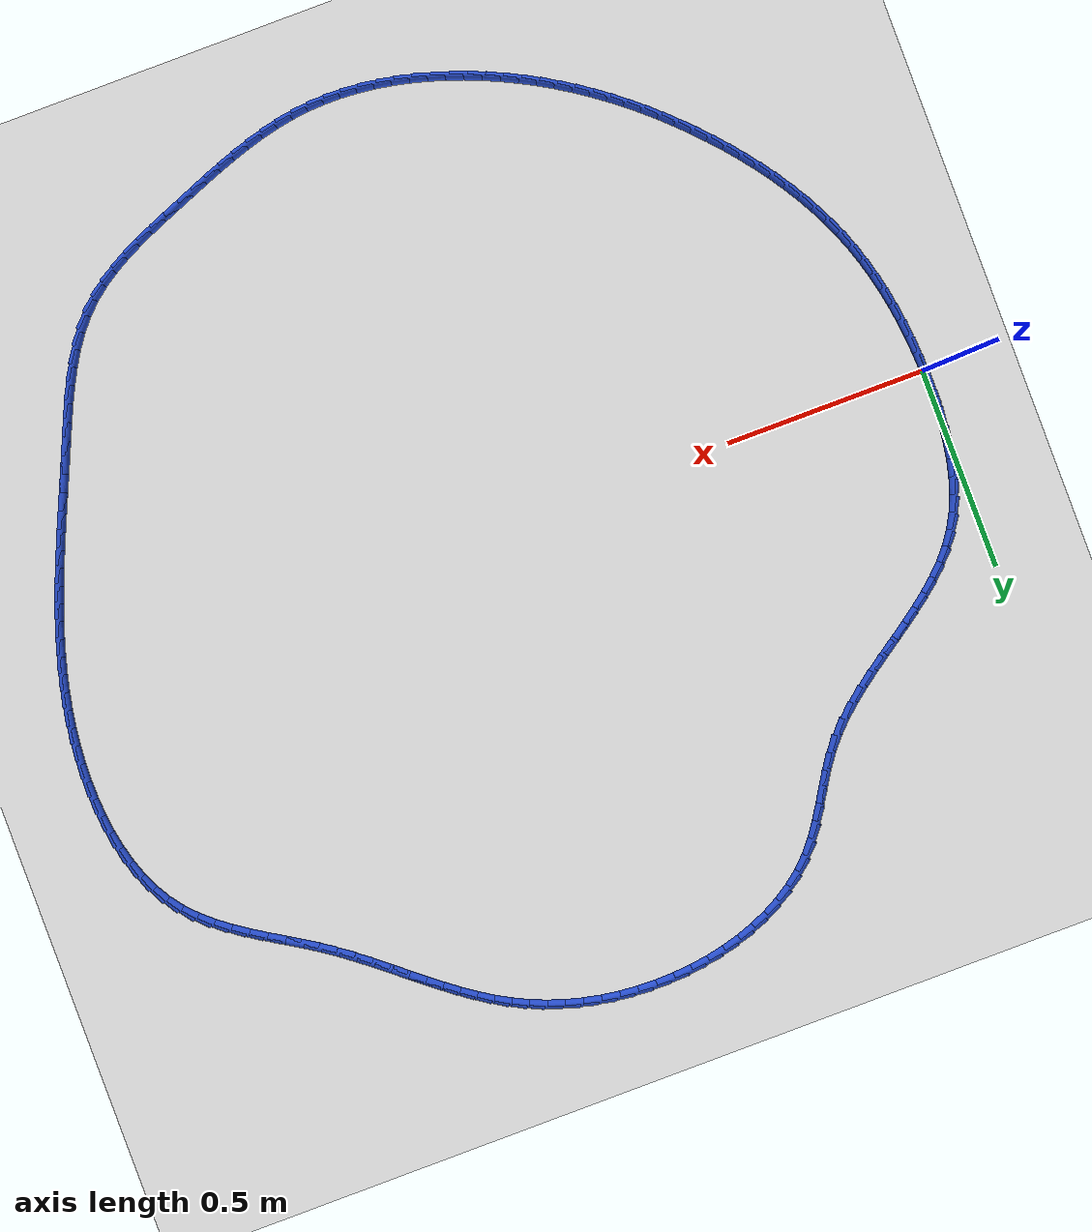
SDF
<sdf version="1.6">
 <world name="default">
  <light name="sun" type="directional">
   <pose>0 0 10 0 -0 0</pose>
   <diffuse>0.8 0.8 0.8 1</diffuse>
   <specular>0.2 0.2 0.2 1</specular>
   <attenuation>
    <range>1000</range>
    <constant>0.9</constant>
    <linear>0.01</linear>
    <quadratic>0.001</quadratic>
   </attenuation>
   <direction>-0.5 0.1 -0.9</direction>
  </light>
  <model name="ground_plane">
   <static>1</static>
   <link name="link">
    <collision name="collision">
     <geometry><plane><normal>0 0 1</normal><size>100 100</size></plane></geometry>
     <surface><friction><ode><mu>100</mu><mu2>50</mu2></ode></friction></surface>
    </collision>
    <visual name="visual">
     <cast_shadows>0</cast_shadows>
     <geometry><plane><normal>0 0 1</normal><size>100 100</size></plane></geometry>
     <material>
      <script><uri>file://media/materials/scripts/gazebo.material</uri><name>Gazebo/WhiteGlow</name></script>
     </material>
    </visual>
   </link>
  </model>
  <gravity>0 0 -9.8</gravity>
  <magnetic_field>6e-06 2.3e-05 -4.2e-05</magnetic_field>
  <atmosphere type="adiabatic"/>
  <physics name="default_physics" default="0" type="ode">
   <max_step_size>0.001</max_step_size>
   <real_time_factor>1</real_time_factor>
   <real_time_update_rate>1000</real_time_update_rate>
  </physics>
  <scene><ambient>0.4 0.4 0.4 1</ambient><background>0.7 0.7 0.7 1</background><shadows>1</shadows></scene>
  <spherical_coordinates>
   <surface_model>EARTH_WGS84</surface_model>
   <latitude_deg>0</latitude_deg>
   <longitude_deg>0</longitude_deg>
   <elevation>0</elevation>
   <heading_deg>0</heading_deg>
  </spherical_coordinates>
  <model name="line">
   <link name="link_0">
    <pose>-6.071532165918825e-18 -1.3877787807814457e-17 0.01 0 1.57 -1.5556435990401796</pose>
    <collision name="collision">
     <geometry><cylinder><radius>0.01</radius><length>0.08</length></cylinder></geometry>
    </collision>
    <visual name="visual">
     <material>
      <script><name>Gazebo/Blue</name><uri>file://media/materials/scripts/gazebo.material</uri></script>
     </material>
     <geometry><cylinder><radius>0.01</radius><length>0.08</length></cylinder></geometry>
    </visual>
   </link>
   <link name="link_1">
    <pose>-0.0006810844086082563 0.044944533552194264 0.01 0 1.57 1.5507419571572678</pose>
    <collision name="collision">
     <geometry><cylinder><radius>0.01</radius><length>0.08</length></cylinder></geometry>
    </collision>
    <visual name="visual">
     <material>
      <script><name>Gazebo/Blue</name><uri>file://media/materials/scripts/gazebo.material</uri></script>
     </material>
     <geometry><cylinder><radius>0.01</radius><length>0.08</length></cylinder></geometry>
    </visual>
   </link>
   <link name="link_2">
    <pose>0.00022326739006194713 0.09003348798143386 0.01 0 1.57 1.5091520987764244</pose>
    <collision name="collision">
     <geometry><cylinder><radius>0.01</radius><length>0.08</length></cylinder></geometry>
    </collision>
    <visual name="visual">
     <material>
      <script><name>Gazebo/Blue</name><uri>file://media/materials/scripts/gazebo.material</uri></script>
     </material>
     <geometry><cylinder><radius>0.01</radius><length>0.08</length></cylinder></geometry>
    </visual>
   </link>
   <link name="link_3">
    <pose>0.002993428314982008 0.13491443213614773 0.01 0 1.57 1.4603209180004186</pose>
    <collision name="collision">
     <geometry><cylinder><radius>0.01</radius><length>0.08</length></cylinder></geometry>
    </collision>
    <visual name="visual">
     <material>
      <script><name>Gazebo/Blue</name><uri>file://media/materials/scripts/gazebo.material</uri></script>
     </material>
     <geometry><cylinder><radius>0.01</radius><length>0.08</length></cylinder></geometry>
    </visual>
   </link>
   <link name="link_4">
    <pose>0.007909771285123334 0.17923493486476474 0.01 0 1.57 1.4032212727957087</pose>
    <collision name="collision">
     <geometry><cylinder><radius>0.01</radius><length>0.08</length></cylinder></geometry>
    </collision>
    <visual name="visual">
     <material>
      <script><name>Gazebo/Blue</name><uri>file://media/materials/scripts/gazebo.material</uri></script>
     </material>
     <geometry><cylinder><radius>0.01</radius><length>0.08</length></cylinder></geometry>
    </visual>
   </link>
   <link name="link_5">
    <pose>0.015252669219457327 0.22264256501571383 0.01 0 1.57 1.3366952583611549</pose>
    <collision name="collision">
     <geometry><cylinder><radius>0.01</radius><length>0.08</length></cylinder></geometry>
    </collision>
    <visual name="visual">
     <material>
      <script><name>Gazebo/Blue</name><uri>file://media/materials/scripts/gazebo.material</uri></script>
     </material>
     <geometry><cylinder><radius>0.01</radius><length>0.08</length></cylinder></geometry>
    </visual>
   </link>
   <link name="link_6">
    <pose>0.025302495036955412 0.2647848914374238 0.01 0 1.57 1.2595438802911676</pose>
    <collision name="collision">
     <geometry><cylinder><radius>0.01</radius><length>0.08</length></cylinder></geometry>
    </collision>
    <visual name="visual">
     <material>
      <script><name>Gazebo/Blue</name><uri>file://media/materials/scripts/gazebo.material</uri></script>
     </material>
     <geometry><cylinder><radius>0.01</radius><length>0.08</length></cylinder></geometry>
    </visual>
   </link>
   <link name="link_7">
    <pose>0.03833962165658896 0.30530948297832355 0.01 0 1.57 1.170702798260568</pose>
    <collision name="collision">
     <geometry><cylinder><radius>0.01</radius><length>0.08</length></cylinder></geometry>
    </collision>
    <visual name="visual">
     <material>
      <script><name>Gazebo/Blue</name><uri>file://media/materials/scripts/gazebo.material</uri></script>
     </material>
     <geometry><cylinder><radius>0.01</radius><length>0.08</length></cylinder></geometry>
    </visual>
   </link>
   <link name="link_8">
    <pose>0.05464442199732939 0.34386390848684195 0.01 0 1.57 1.0695365118263913</pose>
    <collision name="collision">
     <geometry><cylinder><radius>0.01</radius><length>0.08</length></cylinder></geometry>
    </collision>
    <visual name="visual">
     <material>
      <script><name>Gazebo/Blue</name><uri>file://media/materials/scripts/gazebo.material</uri></script>
     </material>
     <geometry><cylinder><radius>0.01</radius><length>0.08</length></cylinder></geometry>
    </visual>
   </link>
   <link name="link_9">
    <pose>0.07449726897814812 0.38009573681140796 0.01 0 1.57 0.9596895195471774</pose>
    <collision name="collision">
     <geometry><cylinder><radius>0.01</radius><length>0.08</length></cylinder></geometry>
    </collision>
    <visual name="visual">
     <material>
      <script><name>Gazebo/Blue</name><uri>file://media/materials/scripts/gazebo.material</uri></script>
     </material>
     <geometry><cylinder><radius>0.01</radius><length>0.08</length></cylinder></geometry>
    </visual>
   </link>
   <link name="link_10">
    <pose>0.09807415052391417 0.41374970725378674 0.01 0 1.57 0.8599576480579803</pose>
    <collision name="collision">
     <geometry><cylinder><radius>0.01</radius><length>0.08</length></cylinder></geometry>
    </collision>
    <visual name="visual">
     <material>
      <script><name>Gazebo/Blue</name><uri>file://media/materials/scripts/gazebo.material</uri></script>
     </material>
     <geometry><cylinder><radius>0.01</radius><length>0.08</length></cylinder></geometry>
    </visual>
   </link>
   <link name="link_11">
    <pose>0.12502897283697698 0.44505655730056204 0.01 0 1.57 0.7772570600761505</pose>
    <collision name="collision">
     <geometry><cylinder><radius>0.01</radius><length>0.08</length></cylinder></geometry>
    </collision>
    <visual name="visual">
     <material>
      <script><name>Gazebo/Blue</name><uri>file://media/materials/scripts/gazebo.material</uri></script>
     </material>
     <geometry><cylinder><radius>0.01</radius><length>0.08</length></cylinder></geometry>
    </visual>
   </link>
   <link name="link_12">
    <pose>0.15485275519003858 0.47439865348167265 0.01 0 1.57 0.7117297020319722</pose>
    <collision name="collision">
     <geometry><cylinder><radius>0.01</radius><length>0.08</length></cylinder></geometry>
    </collision>
    <visual name="visual">
     <material>
      <script><name>Gazebo/Blue</name><uri>file://media/materials/scripts/gazebo.material</uri></script>
     </material>
     <geometry><cylinder><radius>0.01</radius><length>0.08</length></cylinder></geometry>
    </visual>
   </link>
   <link name="link_13">
    <pose>0.18703646300983845 0.5021584124514704 0.01 0 1.57 0.6626610174407837</pose>
    <collision name="collision">
     <geometry><cylinder><radius>0.01</radius><length>0.08</length></cylinder></geometry>
    </collision>
    <visual name="visual">
     <material>
      <script><name>Gazebo/Blue</name><uri>file://media/materials/scripts/gazebo.material</uri></script>
     </material>
     <geometry><cylinder><radius>0.01</radius><length>0.08</length></cylinder></geometry>
    </visual>
   </link>
   <link name="link_14">
    <pose>0.2210710617231165 0.5287182508643081 0.01 0 1.57 0.6290551413989284</pose>
    <collision name="collision">
     <geometry><cylinder><radius>0.01</radius><length>0.08</length></cylinder></geometry>
    </collision>
    <visual name="visual">
     <material>
      <script><name>Gazebo/Blue</name><uri>file://media/materials/scripts/gazebo.material</uri></script>
     </material>
     <geometry><cylinder><radius>0.01</radius><length>0.08</length></cylinder></geometry>
    </visual>
   </link>
   <link name="link_15">
    <pose>0.25644751675661204 0.5544605853745377 0.01 0 1.57 0.6099981581659969</pose>
    <collision name="collision">
     <geometry><cylinder><radius>0.01</radius><length>0.08</length></cylinder></geometry>
    </collision>
    <visual name="visual">
     <material>
      <script><name>Gazebo/Blue</name><uri>file://media/materials/scripts/gazebo.material</uri></script>
     </material>
     <geometry><cylinder><radius>0.01</radius><length>0.08</length></cylinder></geometry>
    </visual>
   </link>
   <link name="link_16">
    <pose>0.292656793537065 0.5797678326365115 0.01 0 1.57 0.6048496134584312</pose>
    <collision name="collision">
     <geometry><cylinder><radius>0.01</radius><length>0.08</length></cylinder></geometry>
    </collision>
    <visual name="visual">
     <material>
      <script><name>Gazebo/Blue</name><uri>file://media/materials/scripts/gazebo.material</uri></script>
     </material>
     <geometry><cylinder><radius>0.01</radius><length>0.08</length></cylinder></geometry>
    </visual>
   </link>
   <link name="link_17">
    <pose>0.32918985749121477 0.6050224093045818 0.01 0 1.57 0.6133219655109351</pose>
    <collision name="collision">
     <geometry><cylinder><radius>0.01</radius><length>0.08</length></cylinder></geometry>
    </collision>
    <visual name="visual">
     <material>
      <script><name>Gazebo/Blue</name><uri>file://media/materials/scripts/gazebo.material</uri></script>
     </material>
     <geometry><cylinder><radius>0.01</radius><length>0.08</length></cylinder></geometry>
    </visual>
   </link>
   <link name="link_18">
    <pose>0.365537674045801 0.6306067320331007 0.01 0 1.57 0.6354893923055147</pose>
    <collision name="collision">
     <geometry><cylinder><radius>0.01</radius><length>0.08</length></cylinder></geometry>
    </collision>
    <visual name="visual">
     <material>
      <script><name>Gazebo/Blue</name><uri>file://media/materials/scripts/gazebo.material</uri></script>
     </material>
     <geometry><cylinder><radius>0.01</radius><length>0.08</length></cylinder></geometry>
    </visual>
   </link>
   <link name="link_19">
    <pose>0.4011912086275633 0.6569032174764204 0.01 0 1.57 0.6717405891738678</pose>
    <collision name="collision">
     <geometry><cylinder><radius>0.01</radius><length>0.08</length></cylinder></geometry>
    </collision>
    <visual name="visual">
     <material>
      <script><name>Gazebo/Blue</name><uri>file://media/materials/scripts/gazebo.material</uri></script>
     </material>
     <geometry><cylinder><radius>0.01</radius><length>0.08</length></cylinder></geometry>
    </visual>
   </link>
   <link name="link_20">
    <pose>0.4356414266632411 0.6842942822888931 0.01 0 1.57 0.7226651045819766</pose>
    <collision name="collision">
     <geometry><cylinder><radius>0.01</radius><length>0.08</length></cylinder></geometry>
    </collision>
    <visual name="visual">
     <material>
      <script><name>Gazebo/Blue</name><uri>file://media/materials/scripts/gazebo.material</uri></script>
     </material>
     <geometry><cylinder><radius>0.01</radius><length>0.08</length></cylinder></geometry>
    </visual>
   </link>
   <link name="link_21">
    <pose>0.46837929357957453 0.7131623431248715 0.01 0 1.57 0.7888432618773925</pose>
    <collision name="collision">
     <geometry><cylinder><radius>0.01</radius><length>0.08</length></cylinder></geometry>
    </collision>
    <visual name="visual">
     <material>
      <script><name>Gazebo/Blue</name><uri>file://media/materials/scripts/gazebo.material</uri></script>
     </material>
     <geometry><cylinder><radius>0.01</radius><length>0.08</length></cylinder></geometry>
    </visual>
   </link>
   <link name="link_22">
    <pose>0.4988957748033028 0.7438898166387076 0.01 0 1.57 0.8704220791844608</pose>
    <collision name="collision">
     <geometry><cylinder><radius>0.01</radius><length>0.08</length></cylinder></geometry>
    </collision>
    <visual name="visual">
     <material>
      <script><name>Gazebo/Blue</name><uri>file://media/materials/scripts/gazebo.material</uri></script>
     </material>
     <geometry><cylinder><radius>0.01</radius><length>0.08</length></cylinder></geometry>
    </visual>
   </link>
   <link name="link_23">
    <pose>0.526684602209757 0.7768568271161431 0.01 0 1.57 0.9526321386942915</pose>
    <collision name="collision">
     <geometry><cylinder><radius>0.01</radius><length>0.08</length></cylinder></geometry>
    </collision>
    <visual name="visual">
     <material>
      <script><name>Gazebo/Blue</name><uri>file://media/materials/scripts/gazebo.material</uri></script>
     </material>
     <geometry><cylinder><radius>0.01</radius><length>0.08</length></cylinder></geometry>
    </visual>
   </link>
   <link name="link_24">
    <pose>0.5517128317124437 0.812051287264964 0.01 0 1.57 1.0047726735013622</pose>
    <collision name="collision">
     <geometry><cylinder><radius>0.01</radius><length>0.08</length></cylinder></geometry>
    </collision>
    <visual name="visual">
     <material>
      <script><name>Gazebo/Blue</name><uri>file://media/materials/scripts/gazebo.material</uri></script>
     </material>
     <geometry><cylinder><radius>0.01</radius><length>0.08</length></cylinder></geometry>
    </visual>
   </link>
   <link name="link_25">
    <pose>0.5749527635990592 0.8486281318530355 0.01 0 1.57 1.0234953961238702</pose>
    <collision name="collision">
     <geometry><cylinder><radius>0.01</radius><length>0.08</length></cylinder></geometry>
    </collision>
    <visual name="visual">
     <material>
      <script><name>Gazebo/Blue</name><uri>file://media/materials/scripts/gazebo.material</uri></script>
     </material>
     <geometry><cylinder><radius>0.01</radius><length>0.08</length></cylinder></geometry>
    </visual>
   </link>
   <link name="link_26">
    <pose>0.5975051736505235 0.8856358367070707 0.01 0 1.57 1.0090250794688906</pose>
    <collision name="collision">
     <geometry><cylinder><radius>0.01</radius><length>0.08</length></cylinder></geometry>
    </collision>
    <visual name="visual">
     <material>
      <script><name>Gazebo/Blue</name><uri>file://media/materials/scripts/gazebo.material</uri></script>
     </material>
     <geometry><cylinder><radius>0.01</radius><length>0.08</length></cylinder></geometry>
    </visual>
   </link>
   <link name="link_27">
    <pose>0.6204708376477565 0.9221228776537832 0.01 0 1.57 0.9606591045515588</pose>
    <collision name="collision">
     <geometry><cylinder><radius>0.01</radius><length>0.08</length></cylinder></geometry>
    </collision>
    <visual name="visual">
     <material>
      <script><name>Gazebo/Blue</name><uri>file://media/materials/scripts/gazebo.material</uri></script>
     </material>
     <geometry><cylinder><radius>0.01</radius><length>0.08</length></cylinder></geometry>
    </visual>
   </link>
   <link name="link_28">
    <pose>0.6449505313716779 0.9571377305198859 0.01 0 1.57 0.8772939229482605</pose>
    <collision name="collision">
     <geometry><cylinder><radius>0.01</radius><length>0.08</length></cylinder></geometry>
    </collision>
    <visual name="visual">
     <material>
      <script><name>Gazebo/Blue</name><uri>file://media/materials/scripts/gazebo.material</uri></script>
     </material>
     <geometry><cylinder><radius>0.01</radius><length>0.08</length></cylinder></geometry>
    </visual>
   </link>
   <link name="link_29">
    <pose>0.6720428835687671 0.9897303723007791 0.01 0 1.57 0.7707152176978957</pose>
    <collision name="collision">
     <geometry><cylinder><radius>0.01</radius><length>0.08</length></cylinder></geometry>
    </collision>
    <visual name="visual">
     <material>
      <script><name>Gazebo/Blue</name><uri>file://media/materials/scripts/gazebo.material</uri></script>
     </material>
     <geometry><cylinder><radius>0.01</radius><length>0.08</length></cylinder></geometry>
    </visual>
   </link>
   <link name="link_30">
    <pose>0.7024324015693675 1.0192403263961836 0.01 0 1.57 0.6678886197364894</pose>
    <collision name="collision">
     <geometry><cylinder><radius>0.01</radius><length>0.08</length></cylinder></geometry>
    </collision>
    <visual name="visual">
     <material>
      <script><name>Gazebo/Blue</name><uri>file://media/materials/scripts/gazebo.material</uri></script>
     </material>
     <geometry><cylinder><radius>0.01</radius><length>0.08</length></cylinder></geometry>
    </visual>
   </link>
   <link name="link_31">
    <pose>0.7358990221644862 1.0456395760036363 0.01 0 1.57 0.572702486377812</pose>
    <collision name="collision">
     <geometry><cylinder><radius>0.01</radius><length>0.08</length></cylinder></geometry>
    </collision>
    <visual name="visual">
     <material>
      <script><name>Gazebo/Blue</name><uri>file://media/materials/scripts/gazebo.material</uri></script>
     </material>
     <geometry><cylinder><radius>0.01</radius><length>0.08</length></cylinder></geometry>
    </visual>
   </link>
   <link name="link_32">
    <pose>0.7721032374635672 1.068983617939421 0.01 0 1.57 0.4850321787184727</pose>
    <collision name="collision">
     <geometry><cylinder><radius>0.01</radius><length>0.08</length></cylinder></geometry>
    </collision>
    <visual name="visual">
     <material>
      <script><name>Gazebo/Blue</name><uri>file://media/materials/scripts/gazebo.material</uri></script>
     </material>
     <geometry><cylinder><radius>0.01</radius><length>0.08</length></cylinder></geometry>
    </visual>
   </link>
   <link name="link_33">
    <pose>0.8107055395760552 1.0893279490198204 0.01 0 1.57 0.4043519719018759</pose>
    <collision name="collision">
     <geometry><cylinder><radius>0.01</radius><length>0.08</length></cylinder></geometry>
    </collision>
    <visual name="visual">
     <material>
      <script><name>Gazebo/Blue</name><uri>file://media/materials/scripts/gazebo.material</uri></script>
     </material>
     <geometry><cylinder><radius>0.01</radius><length>0.08</length></cylinder></geometry>
    </visual>
   </link>
   <link name="link_34">
    <pose>0.8513664206113934 1.1067280660611192 0.01 0 1.57 0.32989888907830317</pose>
    <collision name="collision">
     <geometry><cylinder><radius>0.01</radius><length>0.08</length></cylinder></geometry>
    </collision>
    <visual name="visual">
     <material>
      <script><name>Gazebo/Blue</name><uri>file://media/materials/scripts/gazebo.material</uri></script>
     </material>
     <geometry><cylinder><radius>0.01</radius><length>0.08</length></cylinder></geometry>
    </visual>
   </link>
   <link name="link_35">
    <pose>0.8937463726790258 1.1212394658795997 0.01 0 1.57 0.26079387133389514</pose>
    <collision name="collision">
     <geometry><cylinder><radius>0.01</radius><length>0.08</length></cylinder></geometry>
    </collision>
    <visual name="visual">
     <material>
      <script><name>Gazebo/Blue</name><uri>file://media/materials/scripts/gazebo.material</uri></script>
     </material>
     <geometry><cylinder><radius>0.01</radius><length>0.08</length></cylinder></geometry>
    </visual>
   </link>
   <link name="link_36">
    <pose>0.9375058878883971 1.132917645291546 0.01 0 1.57 0.1961190748766694</pose>
    <collision name="collision">
     <geometry><cylinder><radius>0.01</radius><length>0.08</length></cylinder></geometry>
    </collision>
    <visual name="visual">
     <material>
      <script><name>Gazebo/Blue</name><uri>file://media/materials/scripts/gazebo.material</uri></script>
     </material>
     <geometry><cylinder><radius>0.01</radius><length>0.08</length></cylinder></geometry>
    </visual>
   </link>
   <link name="link_37">
    <pose>0.9823054583489504 1.1418181011132411 0.01 0 1.57 0.13495950097063336</pose>
    <collision name="collision">
     <geometry><cylinder><radius>0.01</radius><length>0.08</length></cylinder></geometry>
    </collision>
    <visual name="visual">
     <material>
      <script><name>Gazebo/Blue</name><uri>file://media/materials/scripts/gazebo.material</uri></script>
     </material>
     <geometry><cylinder><radius>0.01</radius><length>0.08</length></cylinder></geometry>
    </visual>
   </link>
   <link name="link_38">
    <pose>1.0278055761701306 1.1479963301609686 0.01 0 1.57 0.07641893678887425</pose>
    <collision name="collision">
     <geometry><cylinder><radius>0.01</radius><length>0.08</length></cylinder></geometry>
    </collision>
    <visual name="visual">
     <material>
      <script><name>Gazebo/Blue</name><uri>file://media/materials/scripts/gazebo.material</uri></script>
     </material>
     <geometry><cylinder><radius>0.01</radius><length>0.08</length></cylinder></geometry>
    </visual>
   </link>
   <link name="link_39">
    <pose>1.0736667334613808 1.1515078292510126 0.01 0 1.57 0.01961851992147867</pose>
    <collision name="collision">
     <geometry><cylinder><radius>0.01</radius><length>0.08</length></cylinder></geometry>
    </collision>
    <visual name="visual">
     <material>
      <script><name>Gazebo/Blue</name><uri>file://media/materials/scripts/gazebo.material</uri></script>
     </material>
     <geometry><cylinder><radius>0.01</radius><length>0.08</length></cylinder></geometry>
    </visual>
   </link>
   <link name="link_40">
    <pose>1.1195494223321454 1.1524080951996556 0.01 0 1.57 -0.03631631658434748</pose>
    <collision name="collision">
     <geometry><cylinder><radius>0.01</radius><length>0.08</length></cylinder></geometry>
    </collision>
    <visual name="visual">
     <material>
      <script><name>Gazebo/Blue</name><uri>file://media/materials/scripts/gazebo.material</uri></script>
     </material>
     <geometry><cylinder><radius>0.01</radius><length>0.08</length></cylinder></geometry>
    </visual>
   </link>
   <link name="link_41">
    <pose>1.1651141348918688 1.1507526248231816 0.01 0 1.57 -0.09227707807607448</pose>
    <collision name="collision">
     <geometry><cylinder><radius>0.01</radius><length>0.08</length></cylinder></geometry>
    </collision>
    <visual name="visual">
     <material>
      <script><name>Gazebo/Blue</name><uri>file://media/materials/scripts/gazebo.material</uri></script>
     </material>
     <geometry><cylinder><radius>0.01</radius><length>0.08</length></cylinder></geometry>
    </visual>
   </link>
   <link name="link_42">
    <pose>1.2100213633667625 1.146596914921846 0.01 0 1.57 -0.14918624780639053</pose>
    <collision name="collision">
     <geometry><cylinder><radius>0.01</radius><length>0.08</length></cylinder></geometry>
    </collision>
    <visual name="visual">
     <material>
      <script><name>Gazebo/Blue</name><uri>file://media/materials/scripts/gazebo.material</uri></script>
     </material>
     <geometry><cylinder><radius>0.01</radius><length>0.08</length></cylinder></geometry>
    </visual>
   </link>
   <link name="link_43">
    <pose>1.2539786262414898 1.1399900073003981 0.01 0 1.57 -0.20756867615364527</pose>
    <collision name="collision">
     <geometry><cylinder><radius>0.01</radius><length>0.08</length></cylinder></geometry>
    </collision>
    <visual name="visual">
     <material>
      <script><name>Gazebo/Blue</name><uri>file://media/materials/scripts/gazebo.material</uri></script>
     </material>
     <geometry><cylinder><radius>0.01</radius><length>0.08</length></cylinder></geometry>
    </visual>
   </link>
   <link name="link_44">
    <pose>1.2968739595898082 1.1309561652618572 0.01 0 1.57 -0.2674121562361283</pose>
    <collision name="collision">
     <geometry><cylinder><radius>0.01</radius><length>0.08</length></cylinder></geometry>
    </collision>
    <visual name="visual">
     <material>
      <script><name>Gazebo/Blue</name><uri>file://media/materials/scripts/gazebo.material</uri></script>
     </material>
     <geometry><cylinder><radius>0.01</radius><length>0.08</length></cylinder></geometry>
    </visual>
   </link>
   <link name="link_45">
    <pose>1.338638707936685 1.1195137074334982 0.01 0 1.57 -0.3286327748674173</pose>
    <collision name="collision">
     <geometry><cylinder><radius>0.01</radius><length>0.08</length></cylinder></geometry>
    </collision>
    <visual name="visual">
     <material>
      <script><name>Gazebo/Blue</name><uri>file://media/materials/scripts/gazebo.material</uri></script>
     </material>
     <geometry><cylinder><radius>0.01</radius><length>0.08</length></cylinder></geometry>
    </visual>
   </link>
   <link name="link_46">
    <pose>1.3792042158070907 1.1056809524425968 0.01 0 1.57 -0.3911152846077353</pose>
    <collision name="collision">
     <geometry><cylinder><radius>0.01</radius><length>0.08</length></cylinder></geometry>
    </collision>
    <visual name="visual">
     <material>
      <script><name>Gazebo/Blue</name><uri>file://media/materials/scripts/gazebo.material</uri></script>
     </material>
     <geometry><cylinder><radius>0.01</radius><length>0.08</length></cylinder></geometry>
    </visual>
   </link>
   <link name="link_47">
    <pose>1.4185018277259929 1.089476218916428 0.01 0 1.57 -0.45470942995770874</pose>
    <collision name="collision">
     <geometry><cylinder><radius>0.01</radius><length>0.08</length></cylinder></geometry>
    </collision>
    <visual name="visual">
     <material>
      <script><name>Gazebo/Blue</name><uri>file://media/materials/scripts/gazebo.material</uri></script>
     </material>
     <geometry><cylinder><radius>0.01</radius><length>0.08</length></cylinder></geometry>
    </visual>
   </link>
   <link name="link_48">
    <pose>1.4564629646432756 1.0709179039121723 0.01 0 1.57 -0.516883037754754</pose>
    <collision name="collision">
     <geometry><cylinder><radius>0.01</radius><length>0.08</length></cylinder></geometry>
    </collision>
    <visual name="visual">
     <material>
      <script><name>Gazebo/Blue</name><uri>file://media/materials/scripts/gazebo.material</uri></script>
     </material>
     <geometry><cylinder><radius>0.01</radius><length>0.08</length></cylinder></geometry>
    </visual>
   </link>
   <link name="link_49">
    <pose>1.4930904797452682 1.050097710732452 0.01 0 1.57 -0.57052524719998</pose>
    <collision name="collision">
     <geometry><cylinder><radius>0.01</radius><length>0.08</length></cylinder></geometry>
    </collision>
    <visual name="visual">
     <material>
      <script><name>Gazebo/Blue</name><uri>file://media/materials/scripts/gazebo.material</uri></script>
     </material>
     <geometry><cylinder><radius>0.01</radius><length>0.08</length></cylinder></geometry>
    </visual>
   </link>
   <link name="link_50">
    <pose>1.5285911289526872 1.027316594757615 0.01 0 1.57 -0.6140588694752437</pose>
    <collision name="collision">
     <geometry><cylinder><radius>0.01</radius><length>0.08</length></cylinder></geometry>
    </collision>
    <visual name="visual">
     <material>
      <script><name>Gazebo/Blue</name><uri>file://media/materials/scripts/gazebo.material</uri></script>
     </material>
     <geometry><cylinder><radius>0.01</radius><length>0.08</length></cylinder></geometry>
    </visual>
   </link>
   <link name="link_51">
    <pose>1.563207813812154 1.0029126052664503 0.01 0 1.57 -0.6473908055903667</pose>
    <collision name="collision">
     <geometry><cylinder><radius>0.01</radius><length>0.08</length></cylinder></geometry>
    </collision>
    <visual name="visual">
     <material>
      <script><name>Gazebo/Blue</name><uri>file://media/materials/scripts/gazebo.material</uri></script>
     </material>
     <geometry><cylinder><radius>0.01</radius><length>0.08</length></cylinder></geometry>
    </visual>
   </link>
   <link name="link_52">
    <pose>1.5971834358702874 0.9772237915377474 0.01 0 1.57 -0.6706164122329817</pose>
    <collision name="collision">
     <geometry><cylinder><radius>0.01</radius><length>0.08</length></cylinder></geometry>
    </collision>
    <visual name="visual">
     <material>
      <script><name>Gazebo/Blue</name><uri>file://media/materials/scripts/gazebo.material</uri></script>
     </material>
     <geometry><cylinder><radius>0.01</radius><length>0.08</length></cylinder></geometry>
    </visual>
   </link>
   <link name="link_53">
    <pose>1.6307608966737093 0.9505882028502949 0.01 0 1.57 -0.6839144448619148</pose>
    <collision name="collision">
     <geometry><cylinder><radius>0.01</radius><length>0.08</length></cylinder></geometry>
    </collision>
    <visual name="visual">
     <material>
      <script><name>Gazebo/Blue</name><uri>file://media/materials/scripts/gazebo.material</uri></script>
     </material>
     <geometry><cylinder><radius>0.01</radius><length>0.08</length></cylinder></geometry>
    </visual>
   </link>
   <link name="link_54">
    <pose>1.664183097769039 0.9233438884828822 0.01 0 1.57 -0.6874760794268846</pose>
    <collision name="collision">
     <geometry><cylinder><radius>0.01</radius><length>0.08</length></cylinder></geometry>
    </collision>
    <visual name="visual">
     <material>
      <script><name>Gazebo/Blue</name><uri>file://media/materials/scripts/gazebo.material</uri></script>
     </material>
     <geometry><cylinder><radius>0.01</radius><length>0.08</length></cylinder></geometry>
    </visual>
   </link>
   <link name="link_55">
    <pose>1.6976929407028971 0.8958288977142981 0.01 0 1.57 -0.6814669887372637</pose>
    <collision name="collision">
     <geometry><cylinder><radius>0.01</radius><length>0.08</length></cylinder></geometry>
    </collision>
    <visual name="visual">
     <material>
      <script><name>Gazebo/Blue</name><uri>file://media/materials/scripts/gazebo.material</uri></script>
     </material>
     <geometry><cylinder><radius>0.01</radius><length>0.08</length></cylinder></geometry>
    </visual>
   </link>
   <link name="link_56">
    <pose>1.7315333270219044 0.8683812798233315 0.01 0 1.57 -0.6660187672339467</pose>
    <collision name="collision">
     <geometry><cylinder><radius>0.01</radius><length>0.08</length></cylinder></geometry>
    </collision>
    <visual name="visual">
     <material>
      <script><name>Gazebo/Blue</name><uri>file://media/materials/scripts/gazebo.material</uri></script>
     </material>
     <geometry><cylinder><radius>0.01</radius><length>0.08</length></cylinder></geometry>
    </visual>
   </link>
   <link name="link_57">
    <pose>1.7659471582726818 0.8413390840887721 0.01 0 1.57 -0.6412463450030313</pose>
    <collision name="collision">
     <geometry><cylinder><radius>0.01</radius><length>0.08</length></cylinder></geometry>
    </collision>
    <visual name="visual">
     <material>
      <script><name>Gazebo/Blue</name><uri>file://media/materials/scripts/gazebo.material</uri></script>
     </material>
     <geometry><cylinder><radius>0.01</radius><length>0.08</length></cylinder></geometry>
    </visual>
   </link>
   <link name="link_58">
    <pose>1.8011773360018482 0.8150403597894081 0.01 0 1.57 -0.607378121552092</pose>
    <collision name="collision">
     <geometry><cylinder><radius>0.01</radius><length>0.08</length></cylinder></geometry>
    </collision>
    <visual name="visual">
     <material>
      <script><name>Gazebo/Blue</name><uri>file://media/materials/scripts/gazebo.material</uri></script>
     </material>
     <geometry><cylinder><radius>0.01</radius><length>0.08</length></cylinder></geometry>
    </visual>
   </link>
   <link name="link_59">
    <pose>1.837463980495212 0.7898202942725596 0.01 0 1.57 -0.5732715717732695</pose>
    <collision name="collision">
     <geometry><cylinder><radius>0.01</radius><length>0.08</length></cylinder></geometry>
    </collision>
    <visual name="visual">
     <material>
      <script><name>Gazebo/Blue</name><uri>file://media/materials/scripts/gazebo.material</uri></script>
     </material>
     <geometry><cylinder><radius>0.01</radius><length>0.08</length></cylinder></geometry>
    </visual>
   </link>
   <link name="link_60">
    <pose>1.8747741395476392 0.7657330819086782 0.01 0 1.57 -0.5545554981915268</pose>
    <collision name="collision">
     <geometry><cylinder><radius>0.01</radius><length>0.08</length></cylinder></geometry>
    </collision>
    <visual name="visual">
     <material>
      <script><name>Gazebo/Blue</name><uri>file://media/materials/scripts/gazebo.material</uri></script>
     </material>
     <geometry><cylinder><radius>0.01</radius><length>0.08</length></cylinder></geometry>
    </visual>
   </link>
   <link name="link_61">
    <pose>1.9125756202310609 0.7423191958346028 0.01 0 1.57 -0.5526227754636205</pose>
    <collision name="collision">
     <geometry><cylinder><radius>0.01</radius><length>0.08</length></cylinder></geometry>
    </collision>
    <visual name="visual">
     <material>
      <script><name>Gazebo/Blue</name><uri>file://media/materials/scripts/gazebo.material</uri></script>
     </material>
     <geometry><cylinder><radius>0.01</radius><length>0.08</length></cylinder></geometry>
    </visual>
   </link>
   <link name="link_62">
    <pose>1.950282985449193 0.7190643206682892 0.01 0 1.57 -0.5676326543227098</pose>
    <collision name="collision">
     <geometry><cylinder><radius>0.01</radius><length>0.08</length></cylinder></geometry>
    </collision>
    <visual name="visual">
     <material>
      <script><name>Gazebo/Blue</name><uri>file://media/materials/scripts/gazebo.material</uri></script>
     </material>
     <geometry><cylinder><radius>0.01</radius><length>0.08</length></cylinder></geometry>
    </visual>
   </link>
   <link name="link_63">
    <pose>1.987310798105755 0.6954541410276929 0.01 0 1.57 -0.6002501585268075</pose>
    <collision name="collision">
     <geometry><cylinder><radius>0.01</radius><length>0.08</length></cylinder></geometry>
    </collision>
    <visual name="visual">
     <material>
      <script><name>Gazebo/Blue</name><uri>file://media/materials/scripts/gazebo.material</uri></script>
     </material>
     <geometry><cylinder><radius>0.01</radius><length>0.08</length></cylinder></geometry>
    </visual>
   </link>
   <link name="link_64">
    <pose>2.0230736211044653 0.6709743415307695 0.01 0 1.57 -0.6515563831166744</pose>
    <collision name="collision">
     <geometry><cylinder><radius>0.01</radius><length>0.08</length></cylinder></geometry>
    </collision>
    <visual name="visual">
     <material>
      <script><name>Gazebo/Blue</name><uri>file://media/materials/scripts/gazebo.material</uri></script>
     </material>
     <geometry><cylinder><radius>0.01</radius><length>0.08</length></cylinder></geometry>
    </visual>
   </link>
   <link name="link_65">
    <pose>2.0569860173490415 0.645110606795475 0.01 0 1.57 -0.722775224584722</pose>
    <collision name="collision">
     <geometry><cylinder><radius>0.01</radius><length>0.08</length></cylinder></geometry>
    </collision>
    <visual name="visual">
     <material>
      <script><name>Gazebo/Blue</name><uri>file://media/materials/scripts/gazebo.material</uri></script>
     </material>
     <geometry><cylinder><radius>0.01</radius><length>0.08</length></cylinder></geometry>
    </visual>
   </link>
   <link name="link_66">
    <pose>2.088462549743204 0.6173486214397643 0.01 0 1.57 -0.8147147877382126</pose>
    <collision name="collision">
     <geometry><cylinder><radius>0.01</radius><length>0.08</length></cylinder></geometry>
    </collision>
    <visual name="visual">
     <material>
      <script><name>Gazebo/Blue</name><uri>file://media/materials/scripts/gazebo.material</uri></script>
     </material>
     <geometry><cylinder><radius>0.01</radius><length>0.08</length></cylinder></geometry>
    </visual>
   </link>
   <link name="link_67">
    <pose>2.1169177811906685 0.5871740700815936 0.01 0 1.57 -0.9262790079605181</pose>
    <collision name="collision">
     <geometry><cylinder><radius>0.01</radius><length>0.08</length></cylinder></geometry>
    </collision>
    <visual name="visual">
     <material>
      <script><name>Gazebo/Blue</name><uri>file://media/materials/scripts/gazebo.material</uri></script>
     </material>
     <geometry><cylinder><radius>0.01</radius><length>0.08</length></cylinder></geometry>
    </visual>
   </link>
   <link name="link_68">
    <pose>2.1417823449626714 0.5540914112691853 0.01 0 1.57 -1.0414834283191006</pose>
    <collision name="collision">
     <geometry><cylinder><radius>0.01</radius><length>0.08</length></cylinder></geometry>
    </collision>
    <visual name="visual">
     <material>
      <script><name>Gazebo/Blue</name><uri>file://media/materials/scripts/gazebo.material</uri></script>
     </material>
     <geometry><cylinder><radius>0.01</radius><length>0.08</length></cylinder></geometry>
    </visual>
   </link>
   <link name="link_69">
    <pose>2.162866910392255 0.5180490741392406 0.01 0 1.57 -1.1451472210695053</pose>
    <collision name="collision">
     <geometry><cylinder><radius>0.01</radius><length>0.08</length></cylinder></geometry>
    </collision>
    <visual name="visual">
     <material>
      <script><name>Gazebo/Blue</name><uri>file://media/materials/scripts/gazebo.material</uri></script>
     </material>
     <geometry><cylinder><radius>0.01</radius><length>0.08</length></cylinder></geometry>
    </visual>
   </link>
   <link name="link_70">
    <pose>2.1803680621448076 0.4794463267735551 0.01 0 1.57 -1.236939210070047</pose>
    <collision name="collision">
     <geometry><cylinder><radius>0.01</radius><length>0.08</length></cylinder></geometry>
    </collision>
    <visual name="visual">
     <material>
      <script><name>Gazebo/Blue</name><uri>file://media/materials/scripts/gazebo.material</uri></script>
     </material>
     <geometry><cylinder><radius>0.01</radius><length>0.08</length></cylinder></geometry>
    </visual>
   </link>
   <link name="link_71">
    <pose>2.194499631194215 0.43870258495700304 0.01 0 1.57 -1.3178662062581337</pose>
    <collision name="collision">
     <geometry><cylinder><radius>0.01</radius><length>0.08</length></cylinder></geometry>
    </collision>
    <visual name="visual">
     <material>
      <script><name>Gazebo/Blue</name><uri>file://media/materials/scripts/gazebo.material</uri></script>
     </material>
     <geometry><cylinder><radius>0.01</radius><length>0.08</length></cylinder></geometry>
    </visual>
   </link>
   <link name="link_72">
    <pose>2.205475448514361 0.3962372644744599 0.01 0 1.57 -1.3892586507899554</pose>
    <collision name="collision">
     <geometry><cylinder><radius>0.01</radius><length>0.08</length></cylinder></geometry>
    </collision>
    <visual name="visual">
     <material>
      <script><name>Gazebo/Blue</name><uri>file://media/materials/scripts/gazebo.material</uri></script>
     </material>
     <geometry><cylinder><radius>0.01</radius><length>0.08</length></cylinder></geometry>
    </visual>
   </link>
   <link name="link_73">
    <pose>2.2135093450791317 0.3524697811107999 0.01 0 1.57 -1.4525205116610045</pose>
    <collision name="collision">
     <geometry><cylinder><radius>0.01</radius><length>0.08</length></cylinder></geometry>
    </collision>
    <visual name="visual">
     <material>
      <script><name>Gazebo/Blue</name><uri>file://media/materials/scripts/gazebo.material</uri></script>
     </material>
     <geometry><cylinder><radius>0.01</radius><length>0.08</length></cylinder></geometry>
    </visual>
   </link>
   <link name="link_74">
    <pose>2.2188151518624117 0.3078195506508986 0.01 0 1.57 -1.508996877571794</pose>
    <collision name="collision">
     <geometry><cylinder><radius>0.01</radius><length>0.08</length></cylinder></geometry>
    </collision>
    <visual name="visual">
     <material>
      <script><name>Gazebo/Blue</name><uri>file://media/materials/scripts/gazebo.material</uri></script>
     </material>
     <geometry><cylinder><radius>0.01</radius><length>0.08</length></cylinder></geometry>
    </visual>
   </link>
   <link name="link_75">
    <pose>2.2216066998380875 0.2627059888796305 0.01 0 1.57 -1.5599210341685112</pose>
    <collision name="collision">
     <geometry><cylinder><radius>0.01</radius><length>0.08</length></cylinder></geometry>
    </collision>
    <visual name="visual">
     <material>
      <script><name>Gazebo/Blue</name><uri>file://media/materials/scripts/gazebo.material</uri></script>
     </material>
     <geometry><cylinder><radius>0.01</radius><length>0.08</length></cylinder></geometry>
    </visual>
   </link>
   <link name="link_76">
    <pose>2.2220978199800414 0.21754851158186955 0.01 0 1.57 1.5351836940679058</pose>
    <collision name="collision">
     <geometry><cylinder><radius>0.01</radius><length>0.08</length></cylinder></geometry>
    </collision>
    <visual name="visual">
     <material>
      <script><name>Gazebo/Blue</name><uri>file://media/materials/scripts/gazebo.material</uri></script>
     </material>
     <geometry><cylinder><radius>0.01</radius><length>0.08</length></cylinder></geometry>
    </visual>
   </link>
   <link name="link_77">
    <pose>2.220502340917815 0.17276652302370296 0.01 0 1.57 1.4918485956231338</pose>
    <collision name="collision">
     <geometry><cylinder><radius>0.01</radius><length>0.08</length></cylinder></geometry>
    </collision>
    <visual name="visual">
     <material>
      <script><name>Gazebo/Blue</name><uri>file://media/materials/scripts/gazebo.material</uri></script>
     </material>
     <geometry><cylinder><radius>0.01</radius><length>0.08</length></cylinder></geometry>
    </visual>
   </link>
   <link name="link_78">
    <pose>2.217015009320399 0.12868566955088345 0.01 0 1.57 1.4503507819647128</pose>
    <collision name="collision">
     <geometry><cylinder><radius>0.01</radius><length>0.08</length></cylinder></geometry>
    </collision>
    <visual name="visual">
     <material>
      <script><name>Gazebo/Blue</name><uri>file://media/materials/scripts/gazebo.material</uri></script>
     </material>
     <geometry><cylinder><radius>0.01</radius><length>0.08</length></cylinder></geometry>
    </visual>
   </link>
   <link name="link_79">
    <pose>2.2117652988793726 0.0853108831568844 0.01 0 1.57 1.410786194799704</pose>
    <collision name="collision">
     <geometry><cylinder><radius>0.01</radius><length>0.08</length></cylinder></geometry>
    </collision>
    <visual name="visual">
     <material>
      <script><name>Gazebo/Blue</name><uri>file://media/materials/scripts/gazebo.material</uri></script>
     </material>
     <geometry><cylinder><radius>0.01</radius><length>0.08</length></cylinder></geometry>
    </visual>
   </link>
   <link name="link_80">
    <pose>2.204868738259482 0.042578577890626794 0.01 0 1.57 1.3734646343865582</pose>
    <collision name="collision">
     <geometry><cylinder><radius>0.01</radius><length>0.08</length></cylinder></geometry>
    </collision>
    <visual name="visual">
     <material>
      <script><name>Gazebo/Blue</name><uri>file://media/materials/scripts/gazebo.material</uri></script>
     </material>
     <geometry><cylinder><radius>0.01</radius><length>0.08</length></cylinder></geometry>
    </visual>
   </link>
   <link name="link_81">
    <pose>2.1964408561254753 0.00042516780103233134 0.01 0 1.57 1.3386483158262905</pose>
    <collision name="collision">
     <geometry><cylinder><radius>0.01</radius><length>0.08</length></cylinder></geometry>
    </collision>
    <visual name="visual">
     <material>
      <script><name>Gazebo/Blue</name><uri>file://media/materials/scripts/gazebo.material</uri></script>
     </material>
     <geometry><cylinder><radius>0.01</radius><length>0.08</length></cylinder></geometry>
    </visual>
   </link>
   <link name="link_82">
    <pose>2.186597181142099 -0.04121293306297822 0.01 0 1.57 1.306550108630638</pose>
    <collision name="collision">
     <geometry><cylinder><radius>0.01</radius><length>0.08</length></cylinder></geometry>
    </collision>
    <visual name="visual">
     <material>
      <script><name>Gazebo/Blue</name><uri>file://media/materials/scripts/gazebo.material</uri></script>
     </material>
     <geometry><cylinder><radius>0.01</radius><length>0.08</length></cylinder></geometry>
    </visual>
   </link>
   <link name="link_83">
    <pose>2.175453241974101 -0.0823993106524817 0.01 0 1.57 1.2773348397771405</pose>
    <collision name="collision">
     <geometry><cylinder><radius>0.01</radius><length>0.08</length></cylinder></geometry>
    </collision>
    <visual name="visual">
     <material>
      <script><name>Gazebo/Blue</name><uri>file://media/materials/scripts/gazebo.material</uri></script>
     </material>
     <geometry><cylinder><radius>0.01</radius><length>0.08</length></cylinder></geometry>
    </visual>
   </link>
   <link name="link_84">
    <pose>2.1631245672862285 -0.12319755091855733 0.01 0 1.57 1.25112295713858</pose>
    <collision name="collision">
     <geometry><cylinder><radius>0.01</radius><length>0.08</length></cylinder></geometry>
    </collision>
    <visual name="visual">
     <material>
      <script><name>Gazebo/Blue</name><uri>file://media/materials/scripts/gazebo.material</uri></script>
     </material>
     <geometry><cylinder><radius>0.01</radius><length>0.08</length></cylinder></geometry>
    </visual>
   </link>
   <link name="link_85">
    <pose>2.1497266857432287 -0.16367123981228357 0.01 0 1.57 1.2279957565766804</pose>
    <collision name="collision">
     <geometry><cylinder><radius>0.01</radius><length>0.08</length></cylinder></geometry>
    </collision>
    <visual name="visual">
     <material>
      <script><name>Gazebo/Blue</name><uri>file://media/materials/scripts/gazebo.material</uri></script>
     </material>
     <geometry><cylinder><radius>0.01</radius><length>0.08</length></cylinder></geometry>
    </visual>
   </link>
   <link name="link_86">
    <pose>2.135375126009849 -0.20388396328473873 0.01 0 1.57 1.208001410424227</pose>
    <collision name="collision">
     <geometry><cylinder><radius>0.01</radius><length>0.08</length></cylinder></geometry>
    </collision>
    <visual name="visual">
     <material>
      <script><name>Gazebo/Blue</name><uri>file://media/materials/scripts/gazebo.material</uri></script>
     </material>
     <geometry><cylinder><radius>0.01</radius><length>0.08</length></cylinder></geometry>
    </visual>
   </link>
   <link name="link_87">
    <pose>2.1201854167508367 -0.24389930728700207 0.01 0 1.57 1.1911611524413928</pose>
    <collision name="collision">
     <geometry><cylinder><radius>0.01</radius><length>0.08</length></cylinder></geometry>
    </collision>
    <visual name="visual">
     <material>
      <script><name>Gazebo/Blue</name><uri>file://media/materials/scripts/gazebo.material</uri></script>
     </material>
     <geometry><cylinder><radius>0.01</radius><length>0.08</length></cylinder></geometry>
    </visual>
   </link>
   <link name="link_88">
    <pose>2.1042730866309394 -0.2837808577701505 0.01 0 1.57 1.1774751291894925</pose>
    <collision name="collision">
     <geometry><cylinder><radius>0.01</radius><length>0.08</length></cylinder></geometry>
    </collision>
    <visual name="visual">
     <material>
      <script><name>Gazebo/Blue</name><uri>file://media/materials/scripts/gazebo.material</uri></script>
     </material>
     <geometry><cylinder><radius>0.01</radius><length>0.08</length></cylinder></geometry>
    </visual>
   </link>
   <link name="link_89">
    <pose>2.0877536643149037 -0.3235922006852631 0.01 0 1.57 1.166927584554515</pose>
    <collision name="collision">
     <geometry><cylinder><radius>0.01</radius><length>0.08</length></cylinder></geometry>
    </collision>
    <visual name="visual">
     <material>
      <script><name>Gazebo/Blue</name><uri>file://media/materials/scripts/gazebo.material</uri></script>
     </material>
     <geometry><cylinder><radius>0.01</radius><length>0.08</length></cylinder></geometry>
    </visual>
   </link>
   <link name="link_90">
    <pose>2.070742678467478 -0.36339692198341844 0.01 0 1.57 1.1594911807247412</pose>
    <collision name="collision">
     <geometry><cylinder><radius>0.01</radius><length>0.08</length></cylinder></geometry>
    </collision>
    <visual name="visual">
     <material>
      <script><name>Gazebo/Blue</name><uri>file://media/materials/scripts/gazebo.material</uri></script>
     </material>
     <geometry><cylinder><radius>0.01</radius><length>0.08</length></cylinder></geometry>
    </visual>
   </link>
   <link name="link_91">
    <pose>2.0533556577534093 -0.403258607615695 0.01 0 1.57 1.1551303654355667</pose>
    <collision name="collision">
     <geometry><cylinder><radius>0.01</radius><length>0.08</length></cylinder></geometry>
    </collision>
    <visual name="visual">
     <material>
      <script><name>Gazebo/Blue</name><uri>file://media/materials/scripts/gazebo.material</uri></script>
     </material>
     <geometry><cylinder><radius>0.01</radius><length>0.08</length></cylinder></geometry>
    </visual>
   </link>
   <link name="link_92">
    <pose>2.035708130837444 -0.4432408435331716 0.01 0 1.57 1.1538037708779738</pose>
    <collision name="collision">
     <geometry><cylinder><radius>0.01</radius><length>0.08</length></cylinder></geometry>
    </collision>
    <visual name="visual">
     <material>
      <script><name>Gazebo/Blue</name><uri>file://media/materials/scripts/gazebo.material</uri></script>
     </material>
     <geometry><cylinder><radius>0.01</radius><length>0.08</length></cylinder></geometry>
    </visual>
   </link>
   <link name="link_93">
    <pose>2.0179156263843305 -0.4834072156869254 0.01 0 1.57 1.1554656788090165</pose>
    <collision name="collision">
     <geometry><cylinder><radius>0.01</radius><length>0.08</length></cylinder></geometry>
    </collision>
    <visual name="visual">
     <material>
      <script><name>Gazebo/Blue</name><uri>file://media/materials/scripts/gazebo.material</uri></script>
     </material>
     <geometry><cylinder><radius>0.01</radius><length>0.08</length></cylinder></geometry>
    </visual>
   </link>
   <link name="link_94">
    <pose>2.0000936730588164 -0.5238213100280357 0.01 0 1.57 1.159272365273835</pose>
    <collision name="collision">
     <geometry><cylinder><radius>0.01</radius><length>0.08</length></cylinder></geometry>
    </collision>
    <visual name="visual">
     <material>
      <script><name>Gazebo/Blue</name><uri>file://media/materials/scripts/gazebo.material</uri></script>
     </material>
     <geometry><cylinder><radius>0.01</radius><length>0.08</length></cylinder></geometry>
    </visual>
   </link>
   <link name="link_95">
    <pose>1.9823307757599986 -0.5645204308134997 0.01 0 1.57 1.1565465748614017</pose>
    <collision name="collision">
     <geometry><cylinder><radius>0.01</radius><length>0.08</length></cylinder></geometry>
    </collision>
    <visual name="visual">
     <material>
      <script><name>Gazebo/Blue</name><uri>file://media/materials/scripts/gazebo.material</uri></script>
     </material>
     <geometry><cylinder><radius>0.01</radius><length>0.08</length></cylinder></geometry>
    </visual>
   </link>
   <link name="link_96">
    <pose>1.964420182666547 -0.6052547333181036 0.01 0 1.57 1.1419255344002606</pose>
    <collision name="collision">
     <geometry><cylinder><radius>0.01</radius><length>0.08</length></cylinder></geometry>
    </collision>
    <visual name="visual">
     <material>
      <script><name>Gazebo/Blue</name><uri>file://media/materials/scripts/gazebo.material</uri></script>
     </material>
     <geometry><cylinder><radius>0.01</radius><length>0.08</length></cylinder></geometry>
    </visual>
   </link>
   <link name="link_97">
    <pose>1.9459732579769489 -0.6455974833635671 0.01 0 1.57 1.115000253752189</pose>
    <collision name="collision">
     <geometry><cylinder><radius>0.01</radius><length>0.08</length></cylinder></geometry>
    </collision>
    <visual name="visual">
     <material>
      <script><name>Gazebo/Blue</name><uri>file://media/materials/scripts/gazebo.material</uri></script>
     </material>
     <geometry><cylinder><radius>0.01</radius><length>0.08</length></cylinder></geometry>
    </visual>
   </link>
   <link name="link_98">
    <pose>1.9265986986261592 -0.685119352751036 0.01 0 1.57 1.0751210516949843</pose>
    <collision name="collision">
     <geometry><cylinder><radius>0.01</radius><length>0.08</length></cylinder></geometry>
    </collision>
    <visual name="visual">
     <material>
      <script><name>Gazebo/Blue</name><uri>file://media/materials/scripts/gazebo.material</uri></script>
     </material>
     <geometry><cylinder><radius>0.01</radius><length>0.08</length></cylinder></geometry>
    </visual>
   </link>
   <link name="link_99">
    <pose>1.905905201549135 -0.7233910132816553 0.01 0 1.57 1.0214139514335978</pose>
    <collision name="collision">
     <geometry><cylinder><radius>0.01</radius><length>0.08</length></cylinder></geometry>
    </collision>
    <visual name="visual">
     <material>
      <script><name>Gazebo/Blue</name><uri>file://media/materials/scripts/gazebo.material</uri></script>
     </material>
     <geometry><cylinder><radius>0.01</radius><length>0.08</length></cylinder></geometry>
    </visual>
   </link>
   <link name="link_100">
    <pose>1.8835014636808318 -0.7599831367565699 0.01 0 1.57 0.9529631503722887</pose>
    <collision name="collision">
     <geometry><cylinder><radius>0.01</radius><length>0.08</length></cylinder></geometry>
    </collision>
    <visual name="visual">
     <material>
      <script><name>Gazebo/Blue</name><uri>file://media/materials/scripts/gazebo.material</uri></script>
     </material>
     <geometry><cylinder><radius>0.01</radius><length>0.08</length></cylinder></geometry>
    </visual>
   </link>
   <link name="link_101">
    <pose>1.8589961819562049 -0.7944663949769253 0.01 0 1.57 0.8691291193887722</pose>
    <collision name="collision">
     <geometry><cylinder><radius>0.01</radius><length>0.08</length></cylinder></geometry>
    </collision>
    <visual name="visual">
     <material>
      <script><name>Gazebo/Blue</name><uri>file://media/materials/scripts/gazebo.material</uri></script>
     </material>
     <geometry><cylinder><radius>0.01</radius><length>0.08</length></cylinder></geometry>
    </visual>
   </link>
   <link name="link_102">
    <pose>1.8319980533102118 -0.8264114597438659 0.01 0 1.57 0.7702380405950181</pose>
    <collision name="collision">
     <geometry><cylinder><radius>0.01</radius><length>0.08</length></cylinder></geometry>
    </collision>
    <visual name="visual">
     <material>
      <script><name>Gazebo/Blue</name><uri>file://media/materials/scripts/gazebo.material</uri></script>
     </material>
     <geometry><cylinder><radius>0.01</radius><length>0.08</length></cylinder></geometry>
    </visual>
   </link>
   <link name="link_103">
    <pose>1.802121859328572 -0.8553952606084043 0.01 0 1.57 0.6687495687025617</pose>
    <collision name="collision">
     <geometry><cylinder><radius>0.01</radius><length>0.08</length></cylinder></geometry>
    </collision>
    <visual name="visual">
     <material>
      <script><name>Gazebo/Blue</name><uri>file://media/materials/scripts/gazebo.material</uri></script>
     </material>
     <geometry><cylinder><radius>0.01</radius><length>0.08</length></cylinder></geometry>
    </visual>
   </link>
   <link name="link_104">
    <pose>1.7693057177101876 -0.881327261657721 0.01 0 1.57 0.5825405605768036</pose>
    <collision name="collision">
     <geometry><cylinder><radius>0.01</radius><length>0.08</length></cylinder></geometry>
    </collision>
    <visual name="visual">
     <material>
      <script><name>Gazebo/Blue</name><uri>file://media/materials/scripts/gazebo.material</uri></script>
     </material>
     <geometry><cylinder><radius>0.01</radius><length>0.08</length></cylinder></geometry>
    </visual>
   </link>
   <link name="link_105">
    <pose>1.733966283904288 -0.9046090784039568 0.01 0 1.57 0.5130246278094135</pose>
    <collision name="collision">
     <geometry><cylinder><radius>0.01</radius><length>0.08</length></cylinder></geometry>
    </collision>
    <visual name="visual">
     <material>
      <script><name>Gazebo/Blue</name><uri>file://media/materials/scripts/gazebo.material</uri></script>
     </material>
     <geometry><cylinder><radius>0.01</radius><length>0.08</length></cylinder></geometry>
    </visual>
   </link>
   <link name="link_106">
    <pose>1.696558841707172 -0.9256820536243247 0.01 0 1.57 0.4594439207479052</pose>
    <collision name="collision">
     <geometry><cylinder><radius>0.01</radius><length>0.08</length></cylinder></geometry>
    </collision>
    <visual name="visual">
     <material>
      <script><name>Gazebo/Blue</name><uri>file://media/materials/scripts/gazebo.material</uri></script>
     </material>
     <geometry><cylinder><radius>0.01</radius><length>0.08</length></cylinder></geometry>
    </visual>
   </link>
   <link name="link_107">
    <pose>1.6575386749151406 -0.944987530096036 0.01 0 1.57 0.420769685211544</pose>
    <collision name="collision">
     <geometry><cylinder><radius>0.01</radius><length>0.08</length></cylinder></geometry>
    </collision>
    <visual name="visual">
     <material>
      <script><name>Gazebo/Blue</name><uri>file://media/materials/scripts/gazebo.material</uri></script>
     </material>
     <geometry><cylinder><radius>0.01</radius><length>0.08</length></cylinder></geometry>
    </visual>
   </link>
   <link name="link_108">
    <pose>1.6173610673244907 -0.9629668505963026 0.01 0 1.57 0.3960675543929409</pose>
    <collision name="collision">
     <geometry><cylinder><radius>0.01</radius><length>0.08</length></cylinder></geometry>
    </collision>
    <visual name="visual">
     <material>
      <script><name>Gazebo/Blue</name><uri>file://media/materials/scripts/gazebo.material</uri></script>
     </material>
     <geometry><cylinder><radius>0.01</radius><length>0.08</length></cylinder></geometry>
    </visual>
   </link>
   <link name="link_109">
    <pose>1.5764813027315216 -0.9800613579023368 0.01 0 1.57 0.3846995755682915</pose>
    <collision name="collision">
     <geometry><cylinder><radius>0.01</radius><length>0.08</length></cylinder></geometry>
    </collision>
    <visual name="visual">
     <material>
      <script><name>Gazebo/Blue</name><uri>file://media/materials/scripts/gazebo.material</uri></script>
     </material>
     <geometry><cylinder><radius>0.01</radius><length>0.08</length></cylinder></geometry>
    </visual>
   </link>
   <link name="link_110">
    <pose>1.5353546649325327 -0.9967123947913508 0.01 0 1.57 0.3830966818456088</pose>
    <collision name="collision">
     <geometry><cylinder><radius>0.01</radius><length>0.08</length></cylinder></geometry>
    </collision>
    <visual name="visual">
     <material>
      <script><name>Gazebo/Blue</name><uri>file://media/materials/scripts/gazebo.material</uri></script>
     </material>
     <geometry><cylinder><radius>0.01</radius><length>0.08</length></cylinder></geometry>
    </visual>
   </link>
   <link name="link_111">
    <pose>1.4943497888446822 -1.0132376828396994 0.01 0 1.57 0.3776451761244076</pose>
    <collision name="collision">
     <geometry><cylinder><radius>0.01</radius><length>0.08</length></cylinder></geometry>
    </collision>
    <visual name="visual">
     <material>
      <script><name>Gazebo/Blue</name><uri>file://media/materials/scripts/gazebo.material</uri></script>
     </material>
     <geometry><cylinder><radius>0.01</radius><length>0.08</length></cylinder></geometry>
    </visual>
   </link>
   <link name="link_112">
    <pose>1.4534811405801795 -1.0294496540757394 0.01 0 1.57 0.36474771422855873</pose>
    <collision name="collision">
     <geometry><cylinder><radius>0.01</radius><length>0.08</length></cylinder></geometry>
    </collision>
    <visual name="visual">
     <material>
      <script><name>Gazebo/Blue</name><uri>file://media/materials/scripts/gazebo.material</uri></script>
     </material>
     <geometry><cylinder><radius>0.01</radius><length>0.08</length></cylinder></geometry>
    </visual>
   </link>
   <link name="link_113">
    <pose>1.4126727095408893 -1.0450316581935508 0.01 0 1.57 0.34422491939476557</pose>
    <collision name="collision">
     <geometry><cylinder><radius>0.01</radius><length>0.08</length></cylinder></geometry>
    </collision>
    <visual name="visual">
     <material>
      <script><name>Gazebo/Blue</name><uri>file://media/materials/scripts/gazebo.material</uri></script>
     </material>
     <geometry><cylinder><radius>0.01</radius><length>0.08</length></cylinder></geometry>
    </visual>
   </link>
   <link name="link_114">
    <pose>1.3718484850955617 -1.0596670448399637 0.01 0 1.57 0.3158758731033289</pose>
    <collision name="collision">
     <geometry><cylinder><radius>0.01</radius><length>0.08</length></cylinder></geometry>
    </collision>
    <visual name="visual">
     <material>
      <script><name>Gazebo/Blue</name><uri>file://media/materials/scripts/gazebo.material</uri></script>
     </material>
     <geometry><cylinder><radius>0.01</radius><length>0.08</length></cylinder></geometry>
    </visual>
   </link>
   <link name="link_115">
    <pose>1.3309324566129448 -1.0730391636618088 0.01 0 1.57 0.2795135177924136</pose>
    <collision name="collision">
     <geometry><cylinder><radius>0.01</radius><length>0.08</length></cylinder></geometry>
    </collision>
    <visual name="visual">
     <material>
      <script><name>Gazebo/Blue</name><uri>file://media/materials/scripts/gazebo.material</uri></script>
     </material>
     <geometry><cylinder><radius>0.01</radius><length>0.08</length></cylinder></geometry>
    </visual>
   </link>
   <link name="link_116">
    <pose>1.2898486134617875 -1.0848313643059166 0.01 0 1.57 0.23501850627110452</pose>
    <collision name="collision">
     <geometry><cylinder><radius>0.01</radius><length>0.08</length></cylinder></geometry>
    </collision>
    <visual name="visual">
     <material>
      <script><name>Gazebo/Blue</name><uri>file://media/materials/scripts/gazebo.material</uri></script>
     </material>
     <geometry><cylinder><radius>0.01</radius><length>0.08</length></cylinder></geometry>
    </visual>
   </link>
   <link name="link_117">
    <pose>1.2485209450108399 -1.0947269964191175 0.01 0 1.57 0.18241224618610427</pose>
    <collision name="collision">
     <geometry><cylinder><radius>0.01</radius><length>0.08</length></cylinder></geometry>
    </collision>
    <visual name="visual">
     <material>
      <script><name>Gazebo/Blue</name><uri>file://media/materials/scripts/gazebo.material</uri></script>
     </material>
     <geometry><cylinder><radius>0.01</radius><length>0.08</length></cylinder></geometry>
    </visual>
   </link>
   <link name="link_118">
    <pose>1.206873440628851 -1.102409409648242 0.01 0 1.57 0.12195500875876021</pose>
    <collision name="collision">
     <geometry><cylinder><radius>0.01</radius><length>0.08</length></cylinder></geometry>
    </collision>
    <visual name="visual">
     <material>
      <script><name>Gazebo/Blue</name><uri>file://media/materials/scripts/gazebo.material</uri></script>
     </material>
     <geometry><cylinder><radius>0.01</radius><length>0.08</length></cylinder></geometry>
    </visual>
   </link>
   <link name="link_119">
    <pose>1.1648302709159835 -1.1075623567808714 0.01 0 1.57 0.05711761166594266</pose>
    <collision name="collision">
     <geometry><cylinder><radius>0.01</radius><length>0.08</length></cylinder></geometry>
    </collision>
    <visual name="visual">
     <material>
      <script><name>Gazebo/Blue</name><uri>file://media/materials/scripts/gazebo.material</uri></script>
     </material>
     <geometry><cylinder><radius>0.01</radius><length>0.08</length></cylinder></geometry>
    </visual>
   </link>
   <link name="link_120">
    <pose>1.1223698424020705 -1.1099902358773572 0.01 0 1.57 -0.004766423676371933</pose>
    <collision name="collision">
     <geometry><cylinder><radius>0.01</radius><length>0.08</length></cylinder></geometry>
    </collision>
    <visual name="visual">
     <material>
      <script><name>Gazebo/Blue</name><uri>file://media/materials/scripts/gazebo.material</uri></script>
     </material>
     <geometry><cylinder><radius>0.01</radius><length>0.08</length></cylinder></geometry>
    </visual>
   </link>
   <link name="link_121">
    <pose>1.0796004507642607 -1.1097863772926213 0.01 0 1.57 -0.06277770039831199</pose>
    <collision name="collision">
     <geometry><cylinder><radius>0.01</radius><length>0.08</length></cylinder></geometry>
    </collision>
    <visual name="visual">
     <material>
      <script><name>Gazebo/Blue</name><uri>file://media/materials/scripts/gazebo.material</uri></script>
     </material>
     <geometry><cylinder><radius>0.01</radius><length>0.08</length></cylinder></geometry>
    </visual>
   </link>
   <link name="link_122">
    <pose>1.0366494309230476 -1.1070864632822621 0.01 0 1.57 -0.11712797771402937</pose>
    <collision name="collision">
     <geometry><cylinder><radius>0.01</radius><length>0.08</length></cylinder></geometry>
    </collision>
    <visual name="visual">
     <material>
      <script><name>Gazebo/Blue</name><uri>file://media/materials/scripts/gazebo.material</uri></script>
     </material>
     <geometry><cylinder><radius>0.01</radius><length>0.08</length></cylinder></geometry>
    </visual>
   </link>
   <link name="link_123">
    <pose>0.9936441177989223 -1.1020261761018784 0.01 0 1.57 -0.16808434238684916</pose>
    <collision name="collision">
     <geometry><cylinder><radius>0.01</radius><length>0.08</length></cylinder></geometry>
    </collision>
    <visual name="visual">
     <material>
      <script><name>Gazebo/Blue</name><uri>file://media/materials/scripts/gazebo.material</uri></script>
     </material>
     <geometry><cylinder><radius>0.01</radius><length>0.08</length></cylinder></geometry>
    </visual>
   </link>
   <link name="link_124">
    <pose>0.9507118463123772 -1.0947411980070685 0.01 0 1.57 -0.21594687541972785</pose>
    <collision name="collision">
     <geometry><cylinder><radius>0.01</radius><length>0.08</length></cylinder></geometry>
    </collision>
    <visual name="visual">
     <material>
      <script><name>Gazebo/Blue</name><uri>file://media/materials/scripts/gazebo.material</uri></script>
     </material>
     <geometry><cylinder><radius>0.01</radius><length>0.08</length></cylinder></geometry>
    </visual>
   </link>
   <link name="link_125">
    <pose>0.9079799513839042 -1.0853672112534314 0.01 0 1.57 -0.26103235296296673</pose>
    <collision name="collision">
     <geometry><cylinder><radius>0.01</radius><length>0.08</length></cylinder></geometry>
    </collision>
    <visual name="visual">
     <material>
      <script><name>Gazebo/Blue</name><uri>file://media/materials/scripts/gazebo.material</uri></script>
     </material>
     <geometry><cylinder><radius>0.01</radius><length>0.08</length></cylinder></geometry>
    </visual>
   </link>
   <link name="link_126">
    <pose>0.865575767933995 -1.0740398980965657 0.01 0 1.57 -0.3036632955091763</pose>
    <collision name="collision">
     <geometry><cylinder><radius>0.01</radius><length>0.08</length></cylinder></geometry>
    </collision>
    <visual name="visual">
     <material>
      <script><name>Gazebo/Blue</name><uri>file://media/materials/scripts/gazebo.material</uri></script>
     </material>
     <geometry><cylinder><radius>0.01</radius><length>0.08</length></cylinder></geometry>
    </visual>
   </link>
   <link name="link_127">
    <pose>0.8236266308831433 -1.06089494079207 0.01 0 1.57 -0.3441614344299338</pose>
    <collision name="collision">
     <geometry><cylinder><radius>0.01</radius><length>0.08</length></cylinder></geometry>
    </collision>
    <visual name="visual">
     <material>
      <script><name>Gazebo/Blue</name><uri>file://media/materials/scripts/gazebo.material</uri></script>
     </material>
     <geometry><cylinder><radius>0.01</radius><length>0.08</length></cylinder></geometry>
    </visual>
   </link>
   <link name="link_128">
    <pose>0.7822598751518404 -1.0460680215955434 0.01 0 1.57 -0.38284487604236295</pose>
    <collision name="collision">
     <geometry><cylinder><radius>0.01</radius><length>0.08</length></cylinder></geometry>
    </collision>
    <visual name="visual">
     <material>
      <script><name>Gazebo/Blue</name><uri>file://media/materials/scripts/gazebo.material</uri></script>
     </material>
     <geometry><cylinder><radius>0.01</radius><length>0.08</length></cylinder></geometry>
    </visual>
   </link>
   <link name="link_129">
    <pose>0.7416028098062205 -1.0296948032508264 0.01 0 1.57 -0.4202095894191098</pose>
    <collision name="collision">
     <geometry><cylinder><radius>0.01</radius><length>0.08</length></cylinder></geometry>
    </collision>
    <visual name="visual">
     <material>
      <script><name>Gazebo/Blue</name><uri>file://media/materials/scripts/gazebo.material</uri></script>
     </material>
     <geometry><cylinder><radius>0.01</radius><length>0.08</length></cylinder></geometry>
    </visual>
   </link>
   <link name="link_130">
    <pose>0.7017544687707683 -1.0118896098280485 0.01 0 1.57 -0.4569316196711439</pose>
    <collision name="collision">
     <geometry><cylinder><radius>0.01</radius><length>0.08</length></cylinder></geometry>
    </collision>
    <visual name="visual">
     <material>
      <script><name>Gazebo/Blue</name><uri>file://media/materials/scripts/gazebo.material</uri></script>
     </material>
     <geometry><cylinder><radius>0.01</radius><length>0.08</length></cylinder></geometry>
    </visual>
   </link>
   <link name="link_131">
    <pose>0.6627316553565554 -0.9927047076276366 0.01 0 1.57 -0.4930649117595983</pose>
    <collision name="collision">
     <geometry><cylinder><radius>0.01</radius><length>0.08</length></cylinder></geometry>
    </collision>
    <visual name="visual">
     <material>
      <script><name>Gazebo/Blue</name><uri>file://media/materials/scripts/gazebo.material</uri></script>
     </material>
     <geometry><cylinder><radius>0.01</radius><length>0.08</length></cylinder></geometry>
    </visual>
   </link>
   <link name="link_132">
    <pose>0.624536307318428 -0.9721811442174012 0.01 0 1.57 -0.5285610413310684</pose>
    <collision name="collision">
     <geometry><cylinder><radius>0.01</radius><length>0.08</length></cylinder></geometry>
    </collision>
    <visual name="visual">
     <material>
      <script><name>Gazebo/Blue</name><uri>file://media/materials/scripts/gazebo.material</uri></script>
     </material>
     <geometry><cylinder><radius>0.01</radius><length>0.08</length></cylinder></geometry>
    </visual>
   </link>
   <link name="link_133">
    <pose>0.5871703624112307 -0.9503599671651525 0.01 0 1.57 -0.5633799745570102</pose>
    <collision name="collision">
     <geometry><cylinder><radius>0.01</radius><length>0.08</length></cylinder></geometry>
    </collision>
    <visual name="visual">
     <material>
      <script><name>Gazebo/Blue</name><uri>file://media/materials/scripts/gazebo.material</uri></script>
     </material>
     <geometry><cylinder><radius>0.01</radius><length>0.08</length></cylinder></geometry>
    </visual>
   </link>
   <link name="link_134">
    <pose>0.550635758389808 -0.9272822240387006 0.01 0 1.57 -0.59748995071038</pose>
    <collision name="collision">
     <geometry><cylinder><radius>0.01</radius><length>0.08</length></cylinder></geometry>
    </collision>
    <visual name="visual">
     <material>
      <script><name>Gazebo/Blue</name><uri>file://media/materials/scripts/gazebo.material</uri></script>
     </material>
     <geometry><cylinder><radius>0.01</radius><length>0.08</length></cylinder></geometry>
    </visual>
   </link>
   <link name="link_135">
    <pose>0.5149344330090053 -0.9029889624058555 0.01 0 1.57 -0.6308672020288157</pose>
    <collision name="collision">
     <geometry><cylinder><radius>0.01</radius><length>0.08</length></cylinder></geometry>
    </collision>
    <visual name="visual">
     <material>
      <script><name>Gazebo/Blue</name><uri>file://media/materials/scripts/gazebo.material</uri></script>
     </material>
     <geometry><cylinder><radius>0.01</radius><length>0.08</length></cylinder></geometry>
    </visual>
   </link>
   <link name="link_136">
    <pose>0.48006832402366695 -0.877521229834427 0.01 0 1.57 -0.6634955424736059</pose>
    <collision name="collision">
     <geometry><cylinder><radius>0.01</radius><length>0.08</length></cylinder></geometry>
    </collision>
    <visual name="visual">
     <material>
      <script><name>Gazebo/Blue</name><uri>file://media/materials/scripts/gazebo.material</uri></script>
     </material>
     <geometry><cylinder><radius>0.01</radius><length>0.08</length></cylinder></geometry>
    </visual>
   </link>
   <link name="link_137">
    <pose>0.4460393691886388 -0.8509200738922262 0.01 0 1.57 -0.6953658576642986</pose>
    <collision name="collision">
     <geometry><cylinder><radius>0.01</radius><length>0.08</length></cylinder></geometry>
    </collision>
    <visual name="visual">
     <material>
      <script><name>Gazebo/Blue</name><uri>file://media/materials/scripts/gazebo.material</uri></script>
     </material>
     <geometry><cylinder><radius>0.01</radius><length>0.08</length></cylinder></geometry>
    </visual>
   </link>
   <link name="link_138">
    <pose>0.41284950625876526 -0.8232265421470625 0.01 0 1.57 -0.726475527007388</pose>
    <collision name="collision">
     <geometry><cylinder><radius>0.01</radius><length>0.08</length></cylinder></geometry>
    </collision>
    <visual name="visual">
     <material>
      <script><name>Gazebo/Blue</name><uri>file://media/materials/scripts/gazebo.material</uri></script>
     </material>
     <geometry><cylinder><radius>0.01</radius><length>0.08</length></cylinder></geometry>
    </visual>
   </link>
   <link name="link_139">
    <pose>0.38050067298889145 -0.7944816821667462 0.01 0 1.57 -0.756827806341864</pose>
    <collision name="collision">
     <geometry><cylinder><radius>0.01</radius><length>0.08</length></cylinder></geometry>
    </collision>
    <visual name="visual">
     <material>
      <script><name>Gazebo/Blue</name><uri>file://media/materials/scripts/gazebo.material</uri></script>
     </material>
     <geometry><cylinder><radius>0.01</radius><length>0.08</length></cylinder></geometry>
    </visual>
   </link>
   <link name="link_140">
    <pose>0.3489948071338623 -0.7647265415190875 0.01 0 1.57 -0.786431195796482</pose>
    <collision name="collision">
     <geometry><cylinder><radius>0.01</radius><length>0.08</length></cylinder></geometry>
    </collision>
    <visual name="visual">
     <material>
      <script><name>Gazebo/Blue</name><uri>file://media/materials/scripts/gazebo.material</uri></script>
     </material>
     <geometry><cylinder><radius>0.01</radius><length>0.08</length></cylinder></geometry>
    </visual>
   </link>
   <link name="link_141">
    <pose>0.318333846448522 -0.7340021677718956 0.01 0 1.57 -0.815300162007054</pose>
    <collision name="collision">
     <geometry><cylinder><radius>0.01</radius><length>0.08</length></cylinder></geometry>
    </collision>
    <visual name="visual">
     <material>
      <script><name>Gazebo/Blue</name><uri>file://media/materials/scripts/gazebo.material</uri></script>
     </material>
     <geometry><cylinder><radius>0.01</radius><length>0.08</length></cylinder></geometry>
    </visual>
   </link>
   <link name="link_142">
    <pose>0.28851979831014624 -0.7023495968850706 0.01 0 1.57 -0.844080971032143</pose>
    <collision name="collision">
     <geometry><cylinder><radius>0.01</radius><length>0.08</length></cylinder></geometry>
    </collision>
    <visual name="visual">
     <material>
      <script><name>Gazebo/Blue</name><uri>file://media/materials/scripts/gazebo.material</uri></script>
     </material>
     <geometry><cylinder><radius>0.01</radius><length>0.08</length></cylinder></geometry>
    </visual>
   </link>
   <link name="link_143">
    <pose>0.25958660510422793 -0.6698045404027955 0.01 0 1.57 -0.8744771997725389</pose>
    <collision name="collision">
     <geometry><cylinder><radius>0.01</radius><length>0.08</length></cylinder></geometry>
    </collision>
    <visual name="visual">
     <material>
      <script><name>Gazebo/Blue</name><uri>file://media/materials/scripts/gazebo.material</uri></script>
     </material>
     <geometry><cylinder><radius>0.01</radius><length>0.08</length></cylinder></geometry>
    </visual>
   </link>
   <link name="link_144">
    <pose>0.23165066303834417 -0.6363889626228776 0.01 0 1.57 -0.9068941884077272</pose>
    <collision name="collision">
     <geometry><cylinder><radius>0.01</radius><length>0.08</length></cylinder></geometry>
    </collision>
    <visual name="visual">
     <material>
      <script><name>Gazebo/Blue</name><uri>file://media/materials/scripts/gazebo.material</uri></script>
     </material>
     <geometry><cylinder><radius>0.01</radius><length>0.08</length></cylinder></geometry>
    </visual>
   </link>
   <link name="link_145">
    <pose>0.20484149711995994 -0.6021226389228045 0.01 0 1.57 -0.9414866416607948</pose>
    <collision name="collision">
     <geometry><cylinder><radius>0.01</radius><length>0.08</length></cylinder></geometry>
    </collision>
    <visual name="visual">
     <material>
      <script><name>Gazebo/Blue</name><uri>file://media/materials/scripts/gazebo.material</uri></script>
     </material>
     <geometry><cylinder><radius>0.01</radius><length>0.08</length></cylinder></geometry>
    </visual>
   </link>
   <link name="link_146">
    <pose>0.17928863235653983 -0.5670253446800619 0.01 0 1.57 -0.9784099311328991</pose>
    <collision name="collision">
     <geometry><cylinder><radius>0.01</radius><length>0.08</length></cylinder></geometry>
    </collision>
    <visual name="visual">
     <material>
      <script><name>Gazebo/Blue</name><uri>file://media/materials/scripts/gazebo.material</uri></script>
     </material>
     <geometry><cylinder><radius>0.01</radius><length>0.08</length></cylinder></geometry>
    </visual>
   </link>
   <link name="link_147">
    <pose>0.15512159375554974 -0.531116855272138 0.01 0 1.57 -1.017815738618459</pose>
    <collision name="collision">
     <geometry><cylinder><radius>0.01</radius><length>0.08</length></cylinder></geometry>
    </collision>
    <visual name="visual">
     <material>
      <script><name>Gazebo/Blue</name><uri>file://media/materials/scripts/gazebo.material</uri></script>
     </material>
     <geometry><cylinder><radius>0.01</radius><length>0.08</length></cylinder></geometry>
    </visual>
   </link>
   <link name="link_148">
    <pose>0.1324699063244543 -0.494416946076519 0.01 0 1.57 -1.0598461167310094</pose>
    <collision name="collision">
     <geometry><cylinder><radius>0.01</radius><length>0.08</length></cylinder></geometry>
    </collision>
    <visual name="visual">
     <material>
      <script><name>Gazebo/Blue</name><uri>file://media/materials/scripts/gazebo.material</uri></script>
     </material>
     <geometry><cylinder><radius>0.01</radius><length>0.08</length></cylinder></geometry>
    </visual>
   </link>
   <link name="link_149">
    <pose>0.11146309507071854 -0.4569453924706918 0.01 0 1.57 -1.1046257363369267</pose>
    <collision name="collision">
     <geometry><cylinder><radius>0.01</radius><length>0.08</length></cylinder></geometry>
    </collision>
    <visual name="visual">
     <material>
      <script><name>Gazebo/Blue</name><uri>file://media/materials/scripts/gazebo.material</uri></script>
     </material>
     <geometry><cylinder><radius>0.01</radius><length>0.08</length></cylinder></geometry>
    </visual>
   </link>
   <link name="link_150">
    <pose>0.09223068500180744 -0.4187219698321431 0.01 0 1.57 -1.15225188620513</pose>
    <collision name="collision">
     <geometry><cylinder><radius>0.01</radius><length>0.08</length></cylinder></geometry>
    </collision>
    <visual name="visual">
     <material>
      <script><name>Gazebo/Blue</name><uri>file://media/materials/scripts/gazebo.material</uri></script>
     </material>
     <geometry><cylinder><radius>0.01</radius><length>0.08</length></cylinder></geometry>
    </visual>
   </link>
   <link name="link_151">
    <pose>0.07490218688724193 -0.37976645382015345 0.01 0 1.57 -1.2018313744851659</pose>
    <collision name="collision">
     <geometry><cylinder><radius>0.01</radius><length>0.08</length></cylinder></geometry>
    </collision>
    <visual name="visual">
     <material>
      <script><name>Gazebo/Blue</name><uri>file://media/materials/scripts/gazebo.material</uri></script>
     </material>
     <geometry><cylinder><radius>0.01</radius><length>0.08</length></cylinder></geometry>
    </visual>
   </link>
   <link name="link_152">
    <pose>0.05956404095145447 -0.3400994725364026 0.01 0 1.57 -1.2502124668167702</pose>
    <collision name="collision">
     <geometry><cylinder><radius>0.01</radius><length>0.08</length></cylinder></geometry>
    </collision>
    <visual name="visual">
     <material>
      <script><name>Gazebo/Blue</name><uri>file://media/materials/scripts/gazebo.material</uri></script>
     </material>
     <geometry><cylinder><radius>0.01</radius><length>0.08</length></cylinder></geometry>
    </visual>
   </link>
   <link name="link_153">
    <pose>0.046164638623809054 -0.2997443863128118 0.01 0 1.57 -1.2965566969987377</pose>
    <collision name="collision">
     <geometry><cylinder><radius>0.01</radius><length>0.08</length></cylinder></geometry>
    </collision>
    <visual name="visual">
     <material>
      <script><name>Gazebo/Blue</name><uri>file://media/materials/scripts/gazebo.material</uri></script>
     </material>
     <geometry><cylinder><radius>0.01</radius><length>0.08</length></cylinder></geometry>
    </visual>
   </link>
   <link name="link_154">
    <pose>0.03462476986432625 -0.25872510176328367 0.01 0 1.57 -1.3406772687473008</pose>
    <collision name="collision">
     <geometry><cylinder><radius>0.01</radius><length>0.08</length></cylinder></geometry>
    </collision>
    <visual name="visual">
     <material>
      <script><name>Gazebo/Blue</name><uri>file://media/materials/scripts/gazebo.material</uri></script>
     </material>
     <geometry><cylinder><radius>0.01</radius><length>0.08</length></cylinder></geometry>
    </visual>
   </link>
   <link name="link_155">
    <pose>0.024865224633026716 -0.21706552550172148 0.01 0 1.57 -1.3824408896501388</pose>
    <collision name="collision">
     <geometry><cylinder><radius>0.01</radius><length>0.08</length></cylinder></geometry>
    </collision>
    <visual name="visual">
     <material>
      <script><name>Gazebo/Blue</name><uri>file://media/materials/scripts/gazebo.material</uri></script>
     </material>
     <geometry><cylinder><radius>0.01</radius><length>0.08</length></cylinder></geometry>
    </visual>
   </link>
   <link name="link_156">
    <pose>0.01680679288993095 -0.17478956414202731 0.01 0 1.57 -1.4217635145187097</pose>
    <collision name="collision">
     <geometry><cylinder><radius>0.01</radius><length>0.08</length></cylinder></geometry>
    </collision>
    <visual name="visual">
     <material>
      <script><name>Gazebo/Blue</name><uri>file://media/materials/scripts/gazebo.material</uri></script>
     </material>
     <geometry><cylinder><radius>0.01</radius><length>0.08</length></cylinder></geometry>
    </visual>
   </link>
   <link name="link_157">
    <pose>0.010370264595059856 -0.13192112429810557 0.01 0 1.57 -1.458604339473171</pose>
    <collision name="collision">
     <geometry><cylinder><radius>0.01</radius><length>0.08</length></cylinder></geometry>
    </collision>
    <visual name="visual">
     <material>
      <script><name>Gazebo/Blue</name><uri>file://media/materials/scripts/gazebo.material</uri></script>
     </material>
     <geometry><cylinder><radius>0.01</radius><length>0.08</length></cylinder></geometry>
    </visual>
   </link>
   <link name="link_158">
    <pose>0.005476429708433914 -0.08848411258385847 0.01 0 1.57 -1.492958891543374</pose>
    <collision name="collision">
     <geometry><cylinder><radius>0.01</radius><length>0.08</length></cylinder></geometry>
    </collision>
    <visual name="visual">
     <material>
      <script><name>Gazebo/Blue</name><uri>file://media/materials/scripts/gazebo.material</uri></script>
     </material>
     <geometry><cylinder><radius>0.01</radius><length>0.08</length></cylinder></geometry>
    </visual>
   </link>
   <link name="link_159">
    <pose>0.0020460781900737525 -0.04450243561318897 0.01 0 1.57 -1.5248519132397362</pose>
    <collision name="collision">
     <geometry><cylinder><radius>0.01</radius><length>0.08</length></cylinder></geometry>
    </collision>
    <visual name="visual">
     <material>
      <script><name>Gazebo/Blue</name><uri>file://media/materials/scripts/gazebo.material</uri></script>
     </material>
     <geometry><cylinder><radius>0.01</radius><length>0.08</length></cylinder></geometry>
    </visual>
   </link>
   <link name="link_160">
    <pose>-1.734723475976807e-18 -2.7755575615628914e-17 0.01 0 1.57 -1.554330556534828</pose>
    <collision name="collision">
     <geometry><cylinder><radius>0.01</radius><length>0.08</length></cylinder></geometry>
    </collision>
    <visual name="visual">
     <material>
      <script><name>Gazebo/Blue</name><uri>file://media/materials/scripts/gazebo.material</uri></script>
     </material>
     <geometry><cylinder><radius>0.01</radius><length>0.08</length></cylinder></geometry>
    </visual>
   </link>
   <link name="link_161">
    <pose>-0.0007410149017667176 0.044999287641806246 0.01 0 1.57 -1.5543305565348282</pose>
    <collision name="collision">
     <geometry><cylinder><radius>0.01</radius><length>0.08</length></cylinder></geometry>
    </collision>
    <visual name="visual">
     <material>
      <script><name>Gazebo/Blue</name><uri>file://media/materials/scripts/gazebo.material</uri></script>
     </material>
     <geometry><cylinder><radius>0.01</radius><length>0.08</length></cylinder></geometry>
    </visual>
   </link>
  </model>
 </world>
</sdf>
